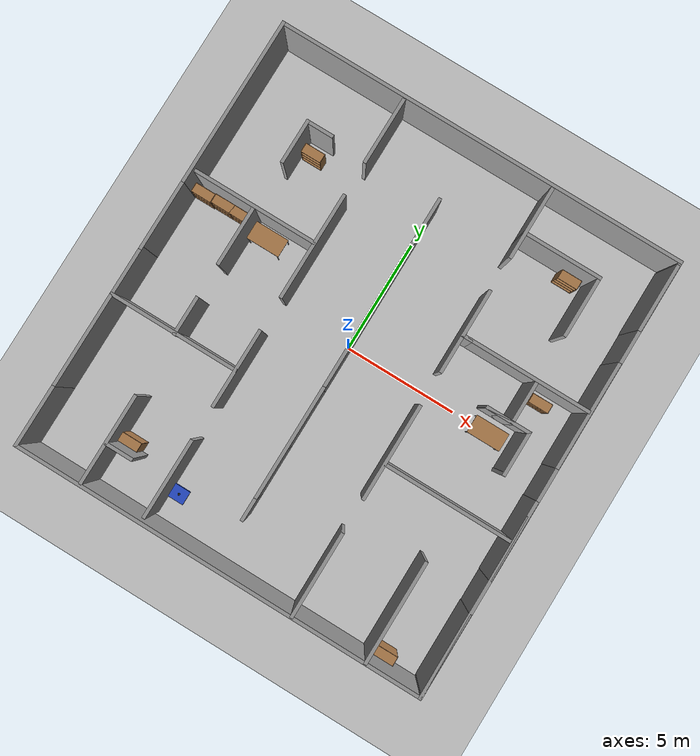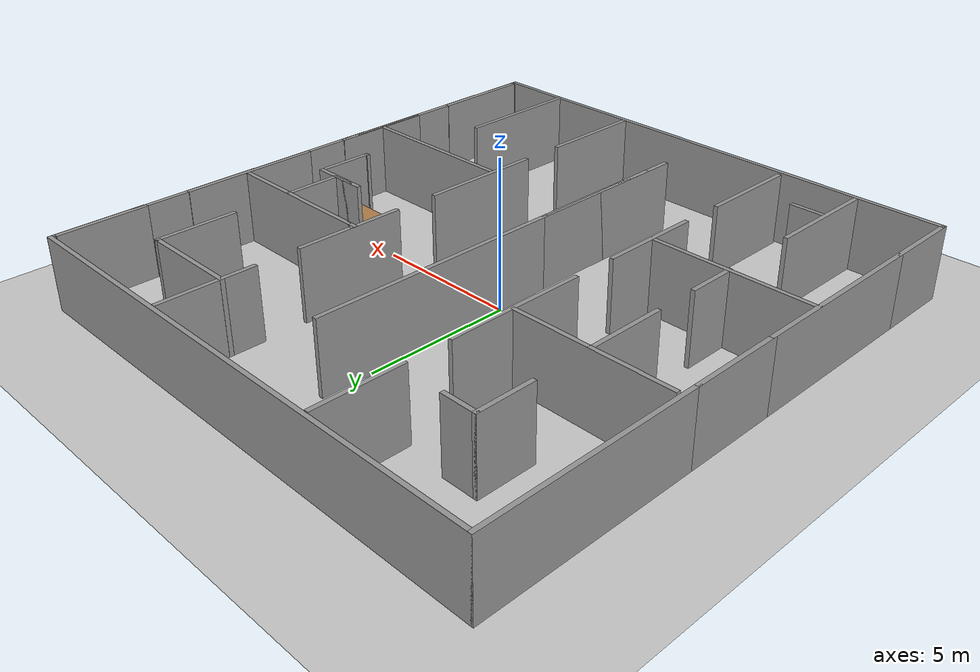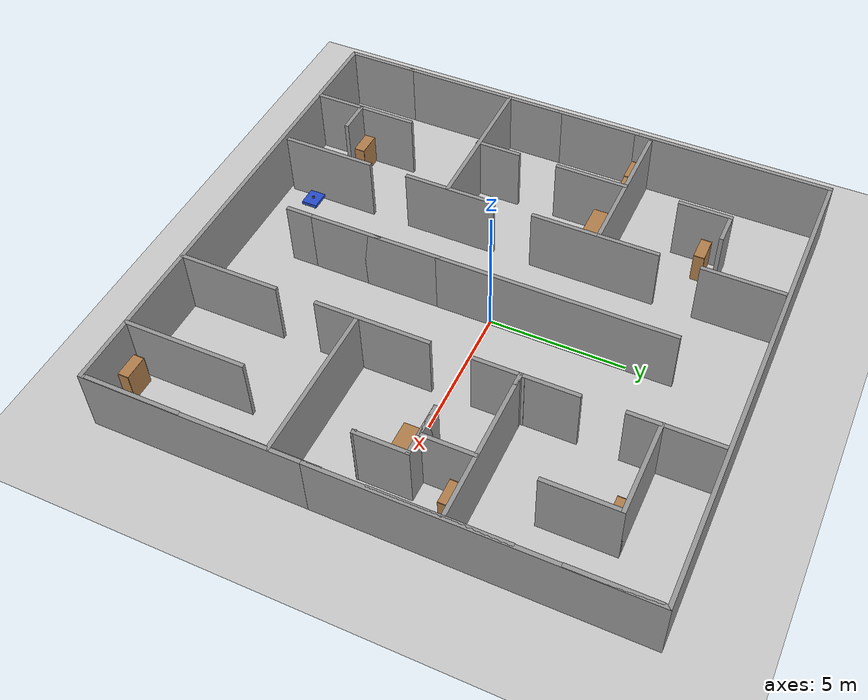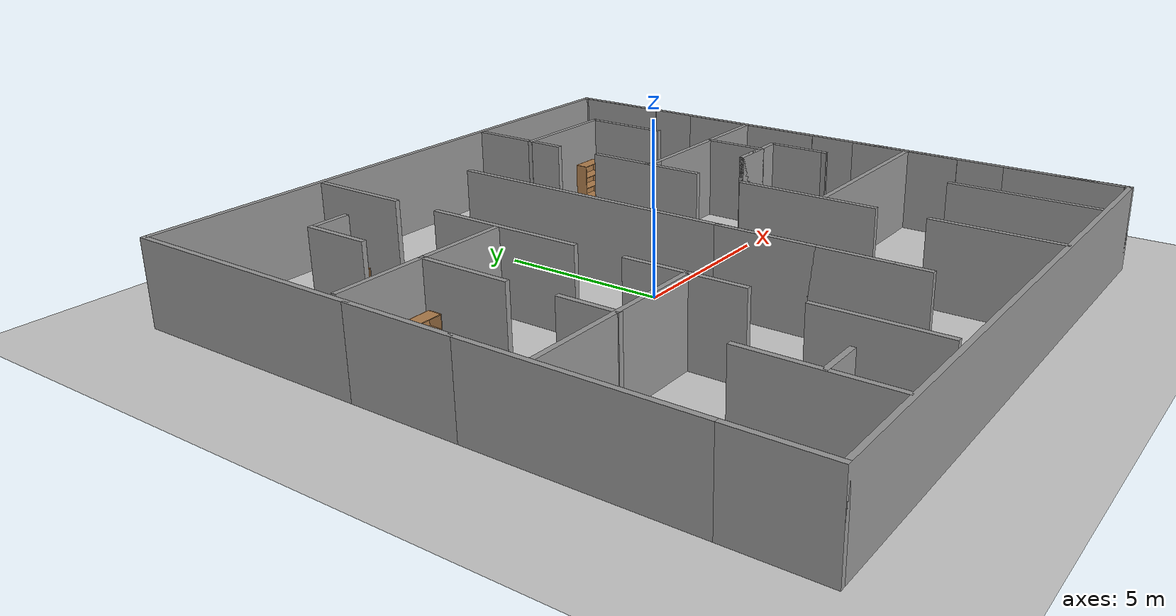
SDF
<sdf version="1.7">
 <world name="default">
  <light name="sun" type="directional">
   <pose>0 0 10 0 -0 0</pose>
   <diffuse>0.8 0.8 0.8 1</diffuse>
   <specular>0.2 0.2 0.2 1</specular>
   <attenuation>
    <range>1000</range>
    <constant>0.9</constant>
    <linear>0.01</linear>
    <quadratic>0.001</quadratic>
   </attenuation>
   <direction>-0.5 0.1 -0.9</direction>
   <spot><inner_angle>0</inner_angle><outer_angle>0</outer_angle><falloff>0</falloff></spot>
  </light>
  <model name="ground_plane">
   <static>1</static>
   <link name="link">
    <collision name="collision">
     <geometry><plane><normal>0 0 1</normal><size>100 100</size></plane></geometry>
     <surface>
      <contact><collide_bitmask>65535</collide_bitmask></contact>
      <friction><ode><mu>100</mu><mu2>50</mu2></ode></friction>
     </surface>
    </collision>
    <visual name="visual">
     <cast_shadows>0</cast_shadows>
     <geometry><plane><normal>0 0 1</normal><size>100 100</size></plane></geometry>
     <material>
      <script><uri>file://media/materials/scripts/gazebo.material</uri><name>Gazebo/Grey</name></script>
     </material>
    </visual>
   </link>
  </model>
  <gravity>0 0 -9.8</gravity>
  <magnetic_field>6e-06 2.3e-05 -4.2e-05</magnetic_field>
  <atmosphere type="adiabatic"/>
  <physics type="ode">
   <max_step_size>0.001</max_step_size>
   <real_time_factor>1</real_time_factor>
   <real_time_update_rate>1000</real_time_update_rate>
  </physics>
  <scene><ambient>0.4 0.4 0.4 1</ambient><background>0.7 0.7 0.7 1</background><shadows>1</shadows></scene>
  <audio><device>default</device></audio>
  <spherical_coordinates>
   <surface_model>EARTH_WGS84</surface_model>
   <latitude_deg>0</latitude_deg>
   <longitude_deg>0</longitude_deg>
   <elevation>0</elevation>
   <heading_deg>0</heading_deg>
  </spherical_coordinates>
  <model name="my_bot">
   <link name="base_link">
    <inertial>
     <pose>0 0 0.0345 0 -0 0</pose>
     <mass>1</mass>
     <inertia>
      <ixx>0.0393076</ixx>
      <ixy>0</ixy>
      <ixz>2.60209e-18</ixz>
      <iyy>0.0647243</iyy>
      <iyz>0</iyz>
      <izz>0.0875577</izz>
     </inertia>
    </inertial>
    <collision name="base_link_fixed_joint_lump__chassis_collision">
     <pose>0 0 0.083 0 -0 0</pose>
     <geometry><box><size>0.7 0.6 0.126</size></box></geometry>
    </collision>
    <collision name="base_link_fixed_joint_lump__caster1_wheel_collision_1">
     <pose>-0.3 0.2 -0.065 0 -0 0</pose>
     <geometry><sphere><radius>0.01</radius></sphere></geometry>
     <surface><friction><ode><mu>0.001</mu><mu2>0.001</mu2></ode></friction></surface>
    </collision>
    <collision name="base_link_fixed_joint_lump__caster2_wheel_collision_2">
     <pose>-0.3 -0.2 -0.065 0 -0 0</pose>
     <geometry><sphere><radius>0.01</radius></sphere></geometry>
     <surface><friction><ode><mu>0.001</mu><mu2>0.001</mu2></ode></friction></surface>
    </collision>
    <collision name="base_link_fixed_joint_lump__caster3_wheel_collision_3">
     <pose>0.3 -0.2 -0.065 0 -0 0</pose>
     <geometry><sphere><radius>0.01</radius></sphere></geometry>
     <surface><friction><ode><mu>0.001</mu><mu2>0.001</mu2></ode></friction></surface>
    </collision>
    <collision name="base_link_fixed_joint_lump__caster4_wheel_collision_4">
     <pose>0.3 0.2 -0.065 0 -0 0</pose>
     <geometry><sphere><radius>0.01</radius></sphere></geometry>
     <surface><friction><ode><mu>0.001</mu><mu2>0.001</mu2></ode></friction></surface>
    </collision>
    <collision name="base_link_fixed_joint_lump__laser_frame_collision_5">
     <pose>0 0 0.19 0 -0 0</pose>
     <geometry><cylinder><length>0.04</length><radius>0.05</radius></cylinder></geometry>
    </collision>
    <visual name="base_link_fixed_joint_lump__chassis_visual">
     <pose>0 0 0.083 0 -0 0</pose>
     <geometry><box><size>0.7 0.6 0.126</size></box></geometry>
     <material>
      <script><name>Gazebo/Blue</name><uri>file://media/materials/scripts/gazebo.material</uri></script>
     </material>
    </visual>
    <visual name="base_link_fixed_joint_lump__caster1_wheel_visual_1">
     <pose>-0.3 0.2 -0.065 0 -0 0</pose>
     <geometry><sphere><radius>0.01</radius></sphere></geometry>
     <material>
      <script><name>Gazebo/Blue</name><uri>file://media/materials/scripts/gazebo.material</uri></script>
     </material>
    </visual>
    <visual name="base_link_fixed_joint_lump__caster2_wheel_visual_2">
     <pose>-0.3 -0.2 -0.065 0 -0 0</pose>
     <geometry><sphere><radius>0.01</radius></sphere></geometry>
     <material>
      <script><name>Gazebo/Blue</name><uri>file://media/materials/scripts/gazebo.material</uri></script>
     </material>
    </visual>
    <visual name="base_link_fixed_joint_lump__caster3_wheel_visual_3">
     <pose>0.3 -0.2 -0.065 0 -0 0</pose>
     <geometry><sphere><radius>0.01</radius></sphere></geometry>
     <material>
      <script><name>Gazebo/Blue</name><uri>file://media/materials/scripts/gazebo.material</uri></script>
     </material>
    </visual>
    <visual name="base_link_fixed_joint_lump__caster4_wheel_visual_4">
     <pose>0.3 0.2 -0.065 0 -0 0</pose>
     <geometry><sphere><radius>0.01</radius></sphere></geometry>
     <material>
      <script><name>Gazebo/Blue</name><uri>file://media/materials/scripts/gazebo.material</uri></script>
     </material>
    </visual>
    <visual name="base_link_fixed_joint_lump__face_link_visual_5">
     <pose>0.35 0.05 0.093 3.14159 1.57079 3.14159</pose>
     <geometry><cylinder><length>0.002</length><radius>0.01</radius></cylinder></geometry>
     <material>
      <script><name>Gazebo/Black</name><uri>file://media/materials/scripts/gazebo.material</uri></script>
     </material>
    </visual>
    <visual name="base_link_fixed_joint_lump__face_link_visual_6">
     <pose>0.35 -0.05 0.093 3.14159 1.57079 3.14159</pose>
     <geometry><cylinder><length>0.002</length><radius>0.01</radius></cylinder></geometry>
     <material>
      <script><name>Gazebo/Black</name><uri>file://media/materials/scripts/gazebo.material</uri></script>
     </material>
    </visual>
    <visual name="base_link_fixed_joint_lump__face_link_visual_7">
     <pose>0.339 0 0.083 0 1.5 0</pose>
     <geometry><cylinder><length>0.02</length><radius>0.03</radius></cylinder></geometry>
     <material>
      <script><name>Gazebo/Black</name><uri>file://media/materials/scripts/gazebo.material</uri></script>
     </material>
    </visual>
    <visual name="base_link_fixed_joint_lump__laser_frame_visual_8">
     <pose>0 0 0.19 0 -0 0</pose>
     <geometry><cylinder><length>0.04</length><radius>0.05</radius></cylinder></geometry>
     <material>
      <script><name>Gazebo/Black</name><uri>file://media/materials/scripts/gazebo.material</uri></script>
     </material>
    </visual>
    <visual name="base_link_fixed_joint_lump__laser_frame_visual_9">
     <pose>0 0 0.14 0 -0 0</pose>
     <geometry><cylinder><length>0.1</length><radius>0.01</radius></cylinder></geometry>
     <material>
      <script><name>Gazebo/Black</name><uri>file://media/materials/scripts/gazebo.material</uri></script>
     </material>
    </visual>
    <sensor name="laser" type="ray">
     <visualize>1</visualize>
     <always_on>1</always_on>
     <update_rate>10</update_rate>
     <ray>
      <scan>
       <horizontal>
        <samples>360</samples>
        <resolution>1</resolution>
        <min_angle>-3.14</min_angle>
        <max_angle>3.14</max_angle>
       </horizontal>
       <vertical><samples>1</samples><min_angle>0</min_angle><max_angle>0</max_angle></vertical>
      </scan>
      <range><min>0.3</min><max>12</max><resolution>0.015</resolution></range>
      <noise><type>gaussian</type><mean>0</mean><stddev>0.01</stddev></noise>
     </ray>
     <plugin name="laser_controller" filename="libgazebo_ros_ray_sensor.so">
      <ros><remapping>~/out:=scan</remapping></ros>
      <output_type>sensor_msgs/LaserScan</output_type>
      <alwaysOn>1</alwaysOn>
      <updateRate>10</updateRate>
      <topicName>scan</topicName>
      <frame_name>laser_frame</frame_name>
      <output_type>sensor_msgs/LaserScan</output_type>
     </plugin>
     <pose>0 0 0.19 0 -0 0</pose>
    </sensor>
   </link>
   <joint name="left_wheel_joint" type="revolute">
    <pose relative_to="base_link">0 0.205 0 -1.5708 0 0</pose>
    <parent>base_link</parent>
    <child>left_wheel</child>
    <axis>
     <xyz>0 0 1</xyz>
     <limit><lower>-1e+16</lower><upper>1e+16</upper></limit>
     <dynamics><spring_reference>0</spring_reference><spring_stiffness>0</spring_stiffness></dynamics>
    </axis>
   </joint>
   <link name="left_wheel">
    <pose relative_to="left_wheel_joint">0 0 0 0 -0 0</pose>
    <inertial>
     <mass>0.05</mass>
     <inertia>
      <ixx>7.69792e-05</ixx>
      <ixy>0</ixy>
      <ixz>0</ixz>
      <iyy>7.69792e-05</iyy>
      <iyz>0</iyz>
      <izz>0.000140625</izz>
     </inertia>
    </inertial>
    <collision name="left_wheel_collision">
     <geometry><sphere><radius>0.075</radius></sphere></geometry>
    </collision>
    <visual name="left_wheel_visual">
     <geometry><cylinder><length>0.04</length><radius>0.075</radius></cylinder></geometry>
     <material>
      <script><name>Gazebo/Black</name><uri>file://media/materials/scripts/gazebo.material</uri></script>
     </material>
    </visual>
   </link>
   <joint name="right_wheel_joint" type="revolute">
    <pose relative_to="base_link">0 -0.205 0 1.5708 -0 0</pose>
    <parent>base_link</parent>
    <child>right_wheel</child>
    <axis>
     <xyz>0 0 -1</xyz>
     <limit><lower>-1e+16</lower><upper>1e+16</upper></limit>
     <dynamics><spring_reference>0</spring_reference><spring_stiffness>0</spring_stiffness></dynamics>
    </axis>
   </joint>
   <link name="right_wheel">
    <pose relative_to="right_wheel_joint">0 0 0 0 -0 0</pose>
    <inertial>
     <mass>0.05</mass>
     <inertia>
      <ixx>7.69792e-05</ixx>
      <ixy>0</ixy>
      <ixz>0</ixz>
      <iyy>7.69792e-05</iyy>
      <iyz>0</iyz>
      <izz>0.000140625</izz>
     </inertia>
    </inertial>
    <collision name="right_wheel_collision">
     <geometry><sphere><radius>0.075</radius></sphere></geometry>
    </collision>
    <visual name="right_wheel_visual">
     <geometry><cylinder><length>0.04</length><radius>0.075</radius></cylinder></geometry>
     <material>
      <script><name>Gazebo/Black</name><uri>file://media/materials/scripts/gazebo.material</uri></script>
     </material>
    </visual>
   </link>
   <static>0</static>
   <plugin name="gazebo_ros2_control" filename="libgazebo_ros2_control.so">
    <parameters>/home/robot/robot/install/ramabot/share/ramabot/config/my_controllers.yaml</parameters>
    <parameters>/home/robot/robot/install/ramabot/share/ramabot/config/gaz_ros2_ctl_use_sim.yaml</parameters>
   </plugin>
   <pose>-2.75861 -8.67534 0.074995 -2.5e-05 -0 -0.001635</pose>
  </model>
  <model name="tembok">
   <pose>0.235969 -0.259973 0 0 -0 0</pose>
   <link name="Wall_0">
    <collision name="Wall_0_Collision">
     <geometry><box><size>6.5 0.15 2.5</size></box></geometry>
     <pose>0 0 1.25 0 -0 0</pose>
    </collision>
    <visual name="Wall_0_Visual">
     <pose>0 0 1.25 0 -0 0</pose>
     <geometry><box><size>6.5 0.15 2.5</size></box></geometry>
     <material>
      <script><uri>file://media/materials/scripts/gazebo.material</uri><name>Gazebo/Grey</name></script>
      <ambient>1 1 1 1</ambient>
     </material>
     <meta><layer>0</layer></meta>
    </visual>
    <pose>-9.05 -3.925 0 0 -0 -1.5708</pose>
   </link>
   <link name="Wall_10">
    <collision name="Wall_10_Collision">
     <geometry><box><size>8 0.15 2.5</size></box></geometry>
     <pose>0 0 1.25 0 -0 0</pose>
    </collision>
    <visual name="Wall_10_Visual">
     <pose>0 0 1.25 0 -0 0</pose>
     <geometry><box><size>8 0.15 2.5</size></box></geometry>
     <material>
      <script><uri>file://media/materials/scripts/gazebo.material</uri><name>Gazebo/Grey</name></script>
      <ambient>1 1 1 1</ambient>
     </material>
     <meta><layer>0</layer></meta>
    </visual>
    <pose>9.05 -5.775 0 0 -0 1.5708</pose>
   </link>
   <link name="Wall_2">
    <collision name="Wall_2_Collision">
     <geometry><box><size>3.25 0.15 2.5</size></box></geometry>
     <pose>0 0 1.25 0 -0 0</pose>
    </collision>
    <visual name="Wall_2_Visual">
     <pose>0 0 1.25 0 -0 0</pose>
     <geometry><box><size>3.25 0.15 2.5</size></box></geometry>
     <material>
      <script><uri>file://media/materials/scripts/gazebo.material</uri><name>Gazebo/Grey</name></script>
      <ambient>1 1 1 1</ambient>
     </material>
     <meta><layer>0</layer></meta>
    </visual>
    <pose>-9.05 0.8 0 0 -0 1.5708</pose>
   </link>
   <link name="Wall_4">
    <collision name="Wall_4_Collision">
     <geometry><box><size>7.5 0.15 2.5</size></box></geometry>
     <pose>0 0 1.25 0 -0 0</pose>
    </collision>
    <visual name="Wall_4_Visual">
     <pose>0 0 1.25 0 -0 0</pose>
     <geometry><box><size>7.5 0.15 2.5</size></box></geometry>
     <material>
      <script><uri>file://media/materials/scripts/gazebo.material</uri><name>Gazebo/Grey</name></script>
      <ambient>1 1 1 1</ambient>
     </material>
     <meta><layer>0</layer></meta>
    </visual>
    <pose>-9.05 6.025 0 0 -0 1.5708</pose>
   </link>
   <link name="Wall_5">
    <collision name="Wall_5_Collision">
     <geometry><box><size>18.25 0.15 2.5</size></box></geometry>
     <pose>0 0 1.25 0 -0 0</pose>
    </collision>
    <visual name="Wall_5_Visual">
     <pose>0 0 1.25 0 -0 0</pose>
     <geometry><box><size>18.25 0.15 2.5</size></box></geometry>
     <material>
      <script><uri>file://media/materials/scripts/gazebo.material</uri><name>Gazebo/Grey</name></script>
      <ambient>1 1 1 1</ambient>
     </material>
     <meta><layer>0</layer></meta>
    </visual>
    <pose>-0 9.7 0 0 -0 0</pose>
   </link>
   <link name="Wall_6">
    <collision name="Wall_6_Collision">
     <geometry><box><size>12 0.15 2.5</size></box></geometry>
     <pose>0 0 1.25 0 -0 0</pose>
    </collision>
    <visual name="Wall_6_Visual">
     <pose>0 0 1.25 0 -0 0</pose>
     <geometry><box><size>12 0.15 2.5</size></box></geometry>
     <material>
      <script><uri>file://media/materials/scripts/gazebo.material</uri><name>Gazebo/Grey</name></script>
      <ambient>1 1 1 1</ambient>
     </material>
     <meta><layer>0</layer></meta>
    </visual>
    <pose>9.05 3.775 0 0 -0 -1.5708</pose>
   </link>
   <link name="Wall_8">
    <collision name="Wall_8_Collision">
     <geometry><box><size>2.75 0.15 2.5</size></box></geometry>
     <pose>0 0 1.25 0 -0 0</pose>
    </collision>
    <visual name="Wall_8_Visual">
     <pose>0 0 1.25 0 -0 0</pose>
     <geometry><box><size>2.75 0.15 2.5</size></box></geometry>
     <material>
      <script><uri>file://media/materials/scripts/gazebo.material</uri><name>Gazebo/Grey</name></script>
      <ambient>1 1 1 1</ambient>
     </material>
     <meta><layer>0</layer></meta>
    </visual>
    <pose>-9.05 -8.4 0 0 -0 -1.5708</pose>
   </link>
   <link name="Wall_9">
    <collision name="Wall_9_Collision">
     <geometry><box><size>18.25 0.15 2.5</size></box></geometry>
     <pose>0 0 1.25 0 -0 0</pose>
    </collision>
    <visual name="Wall_9_Visual">
     <pose>0 0 1.25 0 -0 0</pose>
     <geometry><box><size>18.25 0.15 2.5</size></box></geometry>
     <material>
      <script><uri>file://media/materials/scripts/gazebo.material</uri><name>Gazebo/Grey</name></script>
      <ambient>1 1 1 1</ambient>
     </material>
     <meta><layer>0</layer></meta>
    </visual>
    <pose>-0 -9.7 0 0 -0 0</pose>
   </link>
   <static>1</static>
  </model>
  <model name="samping">
   <pose>-3.71493 -0.202752 0 0 -0 0</pose>
   <link name="Wall_31">
    <collision name="Wall_31_Collision">
     <geometry><box><size>3 0.15 2.5</size></box></geometry>
     <pose>0 0 1.25 0 -0 0</pose>
    </collision>
    <visual name="Wall_31_Visual">
     <pose>0 0 1.25 0 -0 0</pose>
     <geometry><box><size>3 0.15 2.5</size></box></geometry>
     <material>
      <script><uri>file://media/materials/scripts/gazebo.material</uri><name>Gazebo/Grey</name></script>
      <ambient>1 1 1 1</ambient>
     </material>
     <meta><layer>0</layer></meta>
    </visual>
    <pose>0.530829 8.05 0 0 -0 -1.5708</pose>
   </link>
   <link name="Wall_33">
    <collision name="Wall_33_Collision">
     <geometry><box><size>4.75 0.15 2.5</size></box></geometry>
     <pose>0 0 1.25 0 -0 0</pose>
    </collision>
    <visual name="Wall_33_Visual">
     <pose>0 0 1.25 0 -0 0</pose>
     <geometry><box><size>4.75 0.15 2.5</size></box></geometry>
     <material>
      <script><uri>file://media/materials/scripts/gazebo.material</uri><name>Gazebo/Grey</name></script>
      <ambient>1 1 1 1</ambient>
     </material>
     <meta><layer>0</layer></meta>
    </visual>
    <pose>0.530829 2.725 0 0 -0 -1.5708</pose>
   </link>
   <link name="Wall_35">
    <collision name="Wall_35_Collision">
     <geometry><box><size>3.5 0.15 2.5</size></box></geometry>
     <pose>0 0 1.25 0 -0 0</pose>
    </collision>
    <visual name="Wall_35_Visual">
     <pose>0 0 1.25 0 -0 0</pose>
     <geometry><box><size>3.5 0.15 2.5</size></box></geometry>
     <material>
      <script><uri>file://media/materials/scripts/gazebo.material</uri><name>Gazebo/Grey</name></script>
      <ambient>1 1 1 1</ambient>
     </material>
     <meta><layer>0</layer></meta>
    </visual>
    <pose>0.530829 -2.85 0 0 -0 -1.5708</pose>
   </link>
   <link name="Wall_37">
    <collision name="Wall_37_Collision">
     <geometry><box><size>3.5 0.15 2.5</size></box></geometry>
     <pose>0 0 1.25 0 -0 0</pose>
    </collision>
    <visual name="Wall_37_Visual">
     <pose>0 0 1.25 0 -0 0</pose>
     <geometry><box><size>3.5 0.15 2.5</size></box></geometry>
     <material>
      <script><uri>file://media/materials/scripts/gazebo.material</uri><name>Gazebo/Grey</name></script>
      <ambient>1 1 1 1</ambient>
     </material>
     <meta><layer>0</layer></meta>
    </visual>
    <pose>0.530829 -7.8 0 0 -0 -1.5708</pose>
   </link>
   <link name="Wall_39">
    <collision name="Wall_39_Collision">
     <geometry><box><size>5.5 0.15 2.5</size></box></geometry>
     <pose>0 0 1.25 0 -0 0</pose>
    </collision>
    <visual name="Wall_39_Visual">
     <pose>0 0 1.25 0 -0 0</pose>
     <geometry><box><size>5.5 0.15 2.5</size></box></geometry>
     <material>
      <script><uri>file://media/materials/scripts/gazebo.material</uri><name>Gazebo/Grey</name></script>
      <ambient>1 1 1 1</ambient>
     </material>
     <meta><layer>0</layer></meta>
    </visual>
    <pose>-2.19664 2.86376 0 0 -0 3.14159</pose>
   </link>
   <link name="Wall_41">
    <collision name="Wall_41_Collision">
     <geometry><box><size>5.75 0.15 2.5</size></box></geometry>
     <pose>0 0 1.25 0 -0 0</pose>
    </collision>
    <visual name="Wall_41_Visual">
     <pose>0 0 1.25 0 -0 0</pose>
     <geometry><box><size>5.75 0.15 2.5</size></box></geometry>
     <material>
      <script><uri>file://media/materials/scripts/gazebo.material</uri><name>Gazebo/Grey</name></script>
      <ambient>1 1 1 1</ambient>
     </material>
     <meta><layer>0</layer></meta>
    </visual>
    <pose>-2.28666 -2.92545 0 0 -0 3.14159</pose>
   </link>
   <static>1</static>
  </model>
  <model name="samping_0">
   <pose>8.73859 -0.259974 0 0 -0 0</pose>
   <link name="Wall_31">
    <collision name="Wall_31_Collision">
     <geometry><box><size>3 0.15 2.5</size></box></geometry>
     <pose>0 0 1.25 0 -0 0</pose>
    </collision>
    <visual name="Wall_31_Visual">
     <pose>0 0 1.25 0 -0 0</pose>
     <geometry><box><size>3 0.15 2.5</size></box></geometry>
     <material>
      <script><uri>file://media/materials/scripts/gazebo.material</uri><name>Gazebo/Grey</name></script>
      <ambient>1 1 1 1</ambient>
     </material>
     <meta><layer>0</layer></meta>
    </visual>
    <pose>0.530829 8.05 0 0 -0 -1.5708</pose>
   </link>
   <link name="Wall_33">
    <collision name="Wall_33_Collision">
     <geometry><box><size>4.75 0.15 2.5</size></box></geometry>
     <pose>0 0 1.25 0 -0 0</pose>
    </collision>
    <visual name="Wall_33_Visual">
     <pose>0 0 1.25 0 -0 0</pose>
     <geometry><box><size>4.75 0.15 2.5</size></box></geometry>
     <material>
      <script><uri>file://media/materials/scripts/gazebo.material</uri><name>Gazebo/Grey</name></script>
      <ambient>1 1 1 1</ambient>
     </material>
     <meta><layer>0</layer></meta>
    </visual>
    <pose>0.530829 2.725 0 0 -0 -1.5708</pose>
   </link>
   <link name="Wall_35">
    <collision name="Wall_35_Collision">
     <geometry><box><size>3.5 0.15 2.5</size></box></geometry>
     <pose>0 0 1.25 0 -0 0</pose>
    </collision>
    <visual name="Wall_35_Visual">
     <pose>0 0 1.25 0 -0 0</pose>
     <geometry><box><size>3.5 0.15 2.5</size></box></geometry>
     <material>
      <script><uri>file://media/materials/scripts/gazebo.material</uri><name>Gazebo/Grey</name></script>
      <ambient>1 1 1 1</ambient>
     </material>
     <meta><layer>0</layer></meta>
    </visual>
    <pose>0.530829 -2.85 0 0 -0 -1.5708</pose>
   </link>
   <link name="Wall_37">
    <collision name="Wall_37_Collision">
     <geometry><box><size>3.5 0.15 2.5</size></box></geometry>
     <pose>0 0 1.25 0 -0 0</pose>
    </collision>
    <visual name="Wall_37_Visual">
     <pose>0 0 1.25 0 -0 0</pose>
     <geometry><box><size>3.5 0.15 2.5</size></box></geometry>
     <material>
      <script><uri>file://media/materials/scripts/gazebo.material</uri><name>Gazebo/Grey</name></script>
      <ambient>1 1 1 1</ambient>
     </material>
     <meta><layer>0</layer></meta>
    </visual>
    <pose>0.530829 -7.8 0 0 -0 -1.5708</pose>
   </link>
   <link name="Wall_39">
    <collision name="Wall_39_Collision">
     <geometry><box><size>5.5 0.15 2.5</size></box></geometry>
     <pose>0 0 1.25 0 -0 0</pose>
    </collision>
    <visual name="Wall_39_Visual">
     <pose>0 0 1.25 0 -0 0</pose>
     <geometry><box><size>5.5 0.15 2.5</size></box></geometry>
     <material>
      <script><uri>file://media/materials/scripts/gazebo.material</uri><name>Gazebo/Grey</name></script>
      <ambient>1 1 1 1</ambient>
     </material>
     <meta><layer>0</layer></meta>
    </visual>
    <pose>-2.19664 2.86376 0 0 -0 3.14159</pose>
   </link>
   <link name="Wall_41">
    <collision name="Wall_41_Collision">
     <geometry><box><size>5.75 0.15 2.5</size></box></geometry>
     <pose>0 0 1.25 0 -0 0</pose>
    </collision>
    <visual name="Wall_41_Visual">
     <pose>0 0 1.25 0 -0 0</pose>
     <geometry><box><size>5.75 0.15 2.5</size></box></geometry>
     <material>
      <script><uri>file://media/materials/scripts/gazebo.material</uri><name>Gazebo/Grey</name></script>
      <ambient>1 1 1 1</ambient>
     </material>
     <meta><layer>0</layer></meta>
    </visual>
    <pose>-2.28666 -2.92545 0 0 -0 3.14159</pose>
   </link>
   <static>1</static>
  </model>
  <model name="samping3">
   <pose>0.878279 -0.32056 0 0 -0 0</pose>
   <link name="Wall_11">
    <collision name="Wall_11_Collision">
     <geometry><box><size>3.25 0.15 2.5</size></box></geometry>
     <pose>0 0 1.25 0 -0 0</pose>
    </collision>
    <visual name="Wall_11_Visual">
     <pose>0 0 1.25 0 -0 0</pose>
     <geometry><box><size>3.25 0.15 2.5</size></box></geometry>
     <material>
      <script><uri>file://media/materials/scripts/gazebo.material</uri><name>Gazebo/Grey</name></script>
      <ambient>1 1 1 1</ambient>
     </material>
     <meta><layer>0</layer></meta>
    </visual>
    <pose>2.69955 8.05362 0 0 -0 1.5708</pose>
   </link>
   <link name="Wall_2">
    <collision name="Wall_2_Collision">
     <geometry><box><size>4.25 0.15 2.5</size></box></geometry>
     <pose>0 0 1.25 0 -0 0</pose>
    </collision>
    <visual name="Wall_2_Visual">
     <pose>0 0 1.25 0 -0 0</pose>
     <geometry><box><size>4.25 0.15 2.5</size></box></geometry>
     <material>
      <script><uri>file://media/materials/scripts/gazebo.material</uri><name>Gazebo/Grey</name></script>
      <ambient>1 1 1 1</ambient>
     </material>
     <meta><layer>0</layer></meta>
    </visual>
    <pose>2.69955 -2.34638 0 0 -0 -1.5708</pose>
   </link>
   <link name="Wall_21">
    <collision name="Wall_21_Collision">
     <geometry><box><size>0.25 0.15 2.5</size></box></geometry>
     <pose>0 0 1.25 0 -0 0</pose>
    </collision>
    <visual name="Wall_21_Visual">
     <pose>0 0 1.25 0 -0 0</pose>
     <geometry><box><size>0.25 0.15 2.5</size></box></geometry>
     <material>
      <script><uri>file://media/materials/scripts/gazebo.material</uri><name>Gazebo/Grey</name></script>
      <ambient>1 1 1 1</ambient>
     </material>
     <meta><layer>0</layer></meta>
    </visual>
    <pose>2.70984 2.97166 0 0 -0 -1.5708</pose>
   </link>
   <link name="Wall_22">
    <collision name="Wall_22_Collision">
     <geometry><box><size>0.5 0.15 2.5</size></box></geometry>
     <pose>0 0 1.25 0 -0 0</pose>
    </collision>
    <visual name="Wall_22_Visual">
     <pose>0 0 1.25 0 -0 0</pose>
     <geometry><box><size>0.5 0.15 2.5</size></box></geometry>
     <material>
      <script><uri>file://media/materials/scripts/gazebo.material</uri><name>Gazebo/Grey</name></script>
      <ambient>1 1 1 1</ambient>
     </material>
     <meta><layer>0</layer></meta>
    </visual>
    <pose>2.88484 2.92166 0 0 -0 0</pose>
   </link>
   <link name="Wall_24">
    <collision name="Wall_24_Collision">
     <geometry><box><size>3.5 0.15 2.5</size></box></geometry>
     <pose>0 0 1.25 0 -0 0</pose>
    </collision>
    <visual name="Wall_24_Visual">
     <pose>0 0 1.25 0 -0 0</pose>
     <geometry><box><size>3.5 0.15 2.5</size></box></geometry>
     <material>
      <script><uri>file://media/materials/scripts/gazebo.material</uri><name>Gazebo/Grey</name></script>
      <ambient>1 1 1 1</ambient>
     </material>
     <meta><layer>0</layer></meta>
    </visual>
    <pose>4.37148 7.58996 0 0 -0 0</pose>
   </link>
   <link name="Wall_25">
    <collision name="Wall_25_Collision">
     <geometry><box><size>2.75 0.15 2.5</size></box></geometry>
     <pose>0 0 1.25 0 -0 0</pose>
    </collision>
    <visual name="Wall_25_Visual">
     <pose>0 0 1.25 0 -0 0</pose>
     <geometry><box><size>2.75 0.15 2.5</size></box></geometry>
     <material>
      <script><uri>file://media/materials/scripts/gazebo.material</uri><name>Gazebo/Grey</name></script>
      <ambient>1 1 1 1</ambient>
     </material>
     <meta><layer>0</layer></meta>
    </visual>
    <pose>6.04648 6.28996 0 0 -0 -1.5708</pose>
   </link>
   <link name="Wall_28">
    <collision name="Wall_28_Collision">
     <geometry><box><size>2 0.15 2.5</size></box></geometry>
     <pose>0 0 1.25 0 -0 0</pose>
    </collision>
    <visual name="Wall_28_Visual">
     <pose>0 0 1.25 0 -0 0</pose>
     <geometry><box><size>2 0.15 2.5</size></box></geometry>
     <material>
      <script><uri>file://media/materials/scripts/gazebo.material</uri><name>Gazebo/Grey</name></script>
      <ambient>1 1 1 1</ambient>
     </material>
     <meta><layer>0</layer></meta>
    </visual>
    <pose>6.04648 1.96496 0 0 -0 -1.5708</pose>
   </link>
   <link name="Wall_29">
    <collision name="Wall_29_Collision">
     <geometry><box><size>1.25 0.15 2.5</size></box></geometry>
     <pose>0 0 1.25 0 -0 0</pose>
    </collision>
    <visual name="Wall_29_Visual">
     <pose>0 0 1.25 0 -0 0</pose>
     <geometry><box><size>1.25 0.15 2.5</size></box></geometry>
     <material>
      <script><uri>file://media/materials/scripts/gazebo.material</uri><name>Gazebo/Grey</name></script>
      <ambient>1 1 1 1</ambient>
     </material>
     <meta><layer>0</layer></meta>
    </visual>
    <pose>5.49648 1.03996 0 0 -0 3.14159</pose>
   </link>
   <link name="Wall_30">
    <collision name="Wall_30_Collision">
     <geometry><box><size>2 0.15 2.5</size></box></geometry>
     <pose>0 0 1.25 0 -0 0</pose>
    </collision>
    <visual name="Wall_30_Visual">
     <pose>0 0 1.25 0 -0 0</pose>
     <geometry><box><size>2 0.15 2.5</size></box></geometry>
     <material>
      <script><uri>file://media/materials/scripts/gazebo.material</uri><name>Gazebo/Grey</name></script>
      <ambient>1 1 1 1</ambient>
     </material>
     <meta><layer>0</layer></meta>
    </visual>
    <pose>5.87148 1.03996 0 0 -0 0</pose>
   </link>
   <link name="Wall_31">
    <collision name="Wall_31_Collision">
     <geometry><box><size>2 0.15 2.5</size></box></geometry>
     <pose>0 0 1.25 0 -0 0</pose>
    </collision>
    <visual name="Wall_31_Visual">
     <pose>0 0 1.25 0 -0 0</pose>
     <geometry><box><size>2 0.15 2.5</size></box></geometry>
     <material>
      <script><uri>file://media/materials/scripts/gazebo.material</uri><name>Gazebo/Grey</name></script>
      <ambient>1 1 1 1</ambient>
     </material>
     <meta><layer>0</layer></meta>
    </visual>
    <pose>6.79648 0.114957 0 0 -0 -1.5708</pose>
   </link>
   <link name="Wall_33">
    <collision name="Wall_33_Collision">
     <geometry><box><size>0.169397 0.15 2.5</size></box></geometry>
     <pose>0 0 1.25 0 -0 0</pose>
    </collision>
    <visual name="Wall_33_Visual">
     <pose>0 0 1.25 0 -0 0</pose>
     <geometry><box><size>0.169397 0.15 2.5</size></box></geometry>
     <material>
      <script><uri>file://media/materials/scripts/gazebo.material</uri><name>Gazebo/Grey</name></script>
      <ambient>1 1 1 1</ambient>
     </material>
     <meta><layer>0</layer></meta>
    </visual>
    <pose>6.78699 -0.812016 0 0 -0 -2.93676</pose>
   </link>
   <link name="Wall_36">
    <collision name="Wall_36_Collision">
     <geometry><box><size>4.5 0.15 2.5</size></box></geometry>
     <pose>0 0 1.25 0 -0 0</pose>
    </collision>
    <visual name="Wall_36_Visual">
     <pose>0 0 1.25 0 -0 0</pose>
     <geometry><box><size>4.5 0.15 2.5</size></box></geometry>
     <material>
      <script><uri>file://media/materials/scripts/gazebo.material</uri><name>Gazebo/Grey</name></script>
      <ambient>1 1 1 1</ambient>
     </material>
     <meta><layer>0</layer></meta>
    </visual>
    <pose>5.98105 -7.42862 0 0 -0 1.5708</pose>
   </link>
   <link name="Wall_4">
    <collision name="Wall_4_Collision">
     <geometry><box><size>3.75 0.15 2.5</size></box></geometry>
     <pose>0 0 1.25 0 -0 0</pose>
    </collision>
    <visual name="Wall_4_Visual">
     <pose>0 0 1.25 0 -0 0</pose>
     <geometry><box><size>3.75 0.15 2.5</size></box></geometry>
     <material>
      <script><uri>file://media/materials/scripts/gazebo.material</uri><name>Gazebo/Grey</name></script>
      <ambient>1 1 1 1</ambient>
     </material>
     <meta><layer>0</layer></meta>
    </visual>
    <pose>2.69955 -7.79638 0 0 -0 -1.5708</pose>
   </link>
   <link name="Wall_40">
    <collision name="Wall_40_Collision">
     <geometry><box><size>4 0.15 2.5</size></box></geometry>
     <pose>0 0 1.25 0 -0 0</pose>
    </collision>
    <visual name="Wall_40_Visual">
     <pose>0 0 1.25 0 -0 0</pose>
     <geometry><box><size>4 0.15 2.5</size></box></geometry>
     <material>
      <script><uri>file://media/materials/scripts/gazebo.material</uri><name>Gazebo/Grey</name></script>
      <ambient>1 1 1 1</ambient>
     </material>
     <meta><layer>0</layer></meta>
    </visual>
    <pose>-6.81017 -7.60923 0 0 -0 1.5708</pose>
   </link>
   <link name="Wall_45">
    <collision name="Wall_45_Collision">
     <geometry><box><size>2.75 0.15 2.5</size></box></geometry>
     <pose>0 0 1.25 0 -0 0</pose>
    </collision>
    <visual name="Wall_45_Visual">
     <pose>0 0 1.25 0 -0 0</pose>
     <geometry><box><size>2.75 0.15 2.5</size></box></geometry>
     <material>
      <script><uri>file://media/materials/scripts/gazebo.material</uri><name>Gazebo/Grey</name></script>
      <ambient>1 1 1 1</ambient>
     </material>
     <meta><layer>0</layer></meta>
    </visual>
    <pose>-6.81017 1.66577 0 0 -0 1.5708</pose>
   </link>
   <link name="Wall_47">
    <collision name="Wall_47_Collision">
     <geometry><box><size>2 0.15 2.5</size></box></geometry>
     <pose>0 0 1.25 0 -0 0</pose>
    </collision>
    <visual name="Wall_47_Visual">
     <pose>0 0 1.25 0 -0 0</pose>
     <geometry><box><size>2 0.15 2.5</size></box></geometry>
     <material>
      <script><uri>file://media/materials/scripts/gazebo.material</uri><name>Gazebo/Grey</name></script>
      <ambient>1 1 1 1</ambient>
     </material>
     <meta><layer>0</layer></meta>
    </visual>
    <pose>-6.81017 5.99077 0 0 -0 1.5708</pose>
   </link>
   <link name="Wall_48">
    <collision name="Wall_48_Collision">
     <geometry><box><size>1.25 0.15 2.5</size></box></geometry>
     <pose>0 0 1.25 0 -0 0</pose>
    </collision>
    <visual name="Wall_48_Visual">
     <pose>0 0 1.25 0 -0 0</pose>
     <geometry><box><size>1.25 0.15 2.5</size></box></geometry>
     <material>
      <script><uri>file://media/materials/scripts/gazebo.material</uri><name>Gazebo/Grey</name></script>
      <ambient>1 1 1 1</ambient>
     </material>
     <meta><layer>0</layer></meta>
    </visual>
    <pose>-6.26017 6.91577 0 0 -0 0</pose>
   </link>
   <link name="Wall_50">
    <collision name="Wall_50_Collision">
     <geometry><box><size>1.75 0.15 2.5</size></box></geometry>
     <pose>0 0 1.25 0 -0 0</pose>
    </collision>
    <visual name="Wall_50_Visual">
     <pose>0 0 1.25 0 -0 0</pose>
     <geometry><box><size>1.75 0.15 2.5</size></box></geometry>
     <material>
      <script><uri>file://media/materials/scripts/gazebo.material</uri><name>Gazebo/Grey</name></script>
      <ambient>1 1 1 1</ambient>
     </material>
     <meta><layer>0</layer></meta>
    </visual>
    <pose>-6.81017 -2.03423 0 0 -0 1.5708</pose>
   </link>
   <link name="Wall_52">
    <collision name="Wall_52_Collision">
     <geometry><box><size>1.25 0.15 2.5</size></box></geometry>
     <pose>0 0 1.25 0 -0 0</pose>
    </collision>
    <visual name="Wall_52_Visual">
     <pose>0 0 1.25 0 -0 0</pose>
     <geometry><box><size>1.25 0.15 2.5</size></box></geometry>
     <material>
      <script><uri>file://media/materials/scripts/gazebo.material</uri><name>Gazebo/Grey</name></script>
      <ambient>1 1 1 1</ambient>
     </material>
     <meta><layer>0</layer></meta>
    </visual>
    <pose>-6.21391 -7.7763 0 0 -0 0</pose>
   </link>
   <link name="Wall_7">
    <collision name="Wall_7_Collision">
     <geometry><box><size>3.75 0.15 2.5</size></box></geometry>
     <pose>0 0 1.25 0 -0 0</pose>
    </collision>
    <visual name="Wall_7_Visual">
     <pose>0 0 1.25 0 -0 0</pose>
     <geometry><box><size>3.75 0.15 2.5</size></box></geometry>
     <material>
      <script><uri>file://media/materials/scripts/gazebo.material</uri><name>Gazebo/Grey</name></script>
      <ambient>1 1 1 1</ambient>
     </material>
     <meta><layer>0</layer></meta>
    </visual>
    <pose>2.69955 3.10362 0 0 -0 1.5708</pose>
   </link>
   <static>1</static>
  </model>
  <model name="bookshelf">
   <static>1</static>
   <link name="link">
    <inertial><mass>1</mass></inertial>
    <collision name="back">
     <pose>0 0.005 0.6 0 -0 0</pose>
     <geometry><box><size>0.9 0.01 1.2</size></box></geometry>
    </collision>
    <visual name="visual1">
     <pose>0 0.005 0.6 0 -0 0</pose>
     <geometry><box><size>0.9 0.01 1.2</size></box></geometry>
     <material>
      <script><uri>file://media/materials/scripts/gazebo.material</uri><name>Gazebo/Wood</name></script>
     </material>
    </visual>
    <collision name="left_side">
     <pose>0.45 -0.195 0.6 0 -0 0</pose>
     <geometry><box><size>0.02 0.4 1.2</size></box></geometry>
    </collision>
    <visual name="visual2">
     <pose>0.45 -0.195 0.6 0 -0 0</pose>
     <geometry><box><size>0.02 0.4 1.2</size></box></geometry>
     <material>
      <script><uri>file://media/materials/scripts/gazebo.material</uri><name>Gazebo/Wood</name></script>
     </material>
    </visual>
    <collision name="right_side">
     <pose>-0.45 -0.195 0.6 0 -0 0</pose>
     <geometry><box><size>0.02 0.4 1.2</size></box></geometry>
    </collision>
    <visual name="visual3">
     <pose>-0.45 -0.195 0.6 0 -0 0</pose>
     <geometry><box><size>0.02 0.4 1.2</size></box></geometry>
     <material>
      <script><uri>file://media/materials/scripts/gazebo.material</uri><name>Gazebo/Wood</name></script>
     </material>
    </visual>
    <collision name="bottom">
     <pose>0 -0.195 0.03 0 -0 0</pose>
     <geometry><box><size>0.88 0.4 0.06</size></box></geometry>
    </collision>
    <visual name="visual4">
     <pose>0 -0.195 0.03 0 -0 0</pose>
     <geometry><box><size>0.88 0.4 0.06</size></box></geometry>
     <material>
      <script><uri>file://media/materials/scripts/gazebo.material</uri><name>Gazebo/Wood</name></script>
     </material>
    </visual>
    <collision name="top">
     <pose>0 -0.195 1.19 0 -0 0</pose>
     <geometry><box><size>0.88 0.4 0.02</size></box></geometry>
    </collision>
    <visual name="visual5">
     <pose>0 -0.195 1.19 0 -0 0</pose>
     <geometry><box><size>0.88 0.4 0.02</size></box></geometry>
     <material>
      <script><uri>file://media/materials/scripts/gazebo.material</uri><name>Gazebo/Wood</name></script>
     </material>
    </visual>
    <collision name="low_shelf">
     <pose>0 -0.195 0.43 0 -0 0</pose>
     <geometry><box><size>0.88 0.4 0.02</size></box></geometry>
    </collision>
    <visual name="visual6">
     <pose>0 -0.195 0.43 0 -0 0</pose>
     <geometry><box><size>0.88 0.4 0.02</size></box></geometry>
     <material>
      <script><uri>file://media/materials/scripts/gazebo.material</uri><name>Gazebo/Wood</name></script>
     </material>
    </visual>
    <collision name="high_shelf">
     <pose>0 -0.195 0.8 0 -0 0</pose>
     <geometry><box><size>0.88 0.4 0.02</size></box></geometry>
    </collision>
    <visual name="visual7">
     <pose>0 -0.195 0.8 0 -0 0</pose>
     <geometry><box><size>0.88 0.4 0.02</size></box></geometry>
     <material>
      <script><uri>file://media/materials/scripts/gazebo.material</uri><name>Gazebo/Wood</name></script>
     </material>
    </visual>
   </link>
   <pose>6.14593 7.12294 0 0 -0 0</pose>
  </model>
  <model name="bookshelf_0">
   <static>1</static>
   <link name="link">
    <inertial><mass>1</mass></inertial>
    <collision name="back">
     <pose>0 0.005 0.6 0 -0 0</pose>
     <geometry><box><size>0.9 0.01 1.2</size></box></geometry>
    </collision>
    <visual name="visual1">
     <pose>0 0.005 0.6 0 -0 0</pose>
     <geometry><box><size>0.9 0.01 1.2</size></box></geometry>
     <material>
      <script><uri>file://media/materials/scripts/gazebo.material</uri><name>Gazebo/Wood</name></script>
     </material>
    </visual>
    <collision name="left_side">
     <pose>0.45 -0.195 0.6 0 -0 0</pose>
     <geometry><box><size>0.02 0.4 1.2</size></box></geometry>
    </collision>
    <visual name="visual2">
     <pose>0.45 -0.195 0.6 0 -0 0</pose>
     <geometry><box><size>0.02 0.4 1.2</size></box></geometry>
     <material>
      <script><uri>file://media/materials/scripts/gazebo.material</uri><name>Gazebo/Wood</name></script>
     </material>
    </visual>
    <collision name="right_side">
     <pose>-0.45 -0.195 0.6 0 -0 0</pose>
     <geometry><box><size>0.02 0.4 1.2</size></box></geometry>
    </collision>
    <visual name="visual3">
     <pose>-0.45 -0.195 0.6 0 -0 0</pose>
     <geometry><box><size>0.02 0.4 1.2</size></box></geometry>
     <material>
      <script><uri>file://media/materials/scripts/gazebo.material</uri><name>Gazebo/Wood</name></script>
     </material>
    </visual>
    <collision name="bottom">
     <pose>0 -0.195 0.03 0 -0 0</pose>
     <geometry><box><size>0.88 0.4 0.06</size></box></geometry>
    </collision>
    <visual name="visual4">
     <pose>0 -0.195 0.03 0 -0 0</pose>
     <geometry><box><size>0.88 0.4 0.06</size></box></geometry>
     <material>
      <script><uri>file://media/materials/scripts/gazebo.material</uri><name>Gazebo/Wood</name></script>
     </material>
    </visual>
    <collision name="top">
     <pose>0 -0.195 1.19 0 -0 0</pose>
     <geometry><box><size>0.88 0.4 0.02</size></box></geometry>
    </collision>
    <visual name="visual5">
     <pose>0 -0.195 1.19 0 -0 0</pose>
     <geometry><box><size>0.88 0.4 0.02</size></box></geometry>
     <material>
      <script><uri>file://media/materials/scripts/gazebo.material</uri><name>Gazebo/Wood</name></script>
     </material>
    </visual>
    <collision name="low_shelf">
     <pose>0 -0.195 0.43 0 -0 0</pose>
     <geometry><box><size>0.88 0.4 0.02</size></box></geometry>
    </collision>
    <visual name="visual6">
     <pose>0 -0.195 0.43 0 -0 0</pose>
     <geometry><box><size>0.88 0.4 0.02</size></box></geometry>
     <material>
      <script><uri>file://media/materials/scripts/gazebo.material</uri><name>Gazebo/Wood</name></script>
     </material>
    </visual>
    <collision name="high_shelf">
     <pose>0 -0.195 0.8 0 -0 0</pose>
     <geometry><box><size>0.88 0.4 0.02</size></box></geometry>
    </collision>
    <visual name="visual7">
     <pose>0 -0.195 0.8 0 -0 0</pose>
     <geometry><box><size>0.88 0.4 0.02</size></box></geometry>
     <material>
      <script><uri>file://media/materials/scripts/gazebo.material</uri><name>Gazebo/Wood</name></script>
     </material>
    </visual>
   </link>
   <pose>-5.33418 6.12104 0 0 -0 0</pose>
  </model>
  <model name="bookshelf_1">
   <static>1</static>
   <link name="link">
    <inertial><mass>1</mass></inertial>
    <collision name="back">
     <pose>0 0.005 0.6 0 -0 0</pose>
     <geometry><box><size>0.9 0.01 1.2</size></box></geometry>
    </collision>
    <visual name="visual1">
     <pose>0 0.005 0.6 0 -0 0</pose>
     <geometry><box><size>0.9 0.01 1.2</size></box></geometry>
     <material>
      <script><uri>file://media/materials/scripts/gazebo.material</uri><name>Gazebo/Wood</name></script>
     </material>
    </visual>
    <collision name="left_side">
     <pose>0.45 -0.195 0.6 0 -0 0</pose>
     <geometry><box><size>0.02 0.4 1.2</size></box></geometry>
    </collision>
    <visual name="visual2">
     <pose>0.45 -0.195 0.6 0 -0 0</pose>
     <geometry><box><size>0.02 0.4 1.2</size></box></geometry>
     <material>
      <script><uri>file://media/materials/scripts/gazebo.material</uri><name>Gazebo/Wood</name></script>
     </material>
    </visual>
    <collision name="right_side">
     <pose>-0.45 -0.195 0.6 0 -0 0</pose>
     <geometry><box><size>0.02 0.4 1.2</size></box></geometry>
    </collision>
    <visual name="visual3">
     <pose>-0.45 -0.195 0.6 0 -0 0</pose>
     <geometry><box><size>0.02 0.4 1.2</size></box></geometry>
     <material>
      <script><uri>file://media/materials/scripts/gazebo.material</uri><name>Gazebo/Wood</name></script>
     </material>
    </visual>
    <collision name="bottom">
     <pose>0 -0.195 0.03 0 -0 0</pose>
     <geometry><box><size>0.88 0.4 0.06</size></box></geometry>
    </collision>
    <visual name="visual4">
     <pose>0 -0.195 0.03 0 -0 0</pose>
     <geometry><box><size>0.88 0.4 0.06</size></box></geometry>
     <material>
      <script><uri>file://media/materials/scripts/gazebo.material</uri><name>Gazebo/Wood</name></script>
     </material>
    </visual>
    <collision name="top">
     <pose>0 -0.195 1.19 0 -0 0</pose>
     <geometry><box><size>0.88 0.4 0.02</size></box></geometry>
    </collision>
    <visual name="visual5">
     <pose>0 -0.195 1.19 0 -0 0</pose>
     <geometry><box><size>0.88 0.4 0.02</size></box></geometry>
     <material>
      <script><uri>file://media/materials/scripts/gazebo.material</uri><name>Gazebo/Wood</name></script>
     </material>
    </visual>
    <collision name="low_shelf">
     <pose>0 -0.195 0.43 0 -0 0</pose>
     <geometry><box><size>0.88 0.4 0.02</size></box></geometry>
    </collision>
    <visual name="visual6">
     <pose>0 -0.195 0.43 0 -0 0</pose>
     <geometry><box><size>0.88 0.4 0.02</size></box></geometry>
     <material>
      <script><uri>file://media/materials/scripts/gazebo.material</uri><name>Gazebo/Wood</name></script>
     </material>
    </visual>
    <collision name="high_shelf">
     <pose>0 -0.195 0.8 0 -0 0</pose>
     <geometry><box><size>0.88 0.4 0.02</size></box></geometry>
    </collision>
    <visual name="visual7">
     <pose>0 -0.195 0.8 0 -0 0</pose>
     <geometry><box><size>0.88 0.4 0.02</size></box></geometry>
     <material>
      <script><uri>file://media/materials/scripts/gazebo.material</uri><name>Gazebo/Wood</name></script>
     </material>
    </visual>
   </link>
   <pose>7.69195 2.25546 0 0 -0 0</pose>
  </model>
  <model name="bookshelf_2">
   <static>1</static>
   <link name="link">
    <inertial><mass>1</mass></inertial>
    <collision name="back">
     <pose>0 0.005 0.6 0 -0 0</pose>
     <geometry><box><size>0.9 0.01 1.2</size></box></geometry>
    </collision>
    <visual name="visual1">
     <pose>0 0.005 0.6 0 -0 0</pose>
     <geometry><box><size>0.9 0.01 1.2</size></box></geometry>
     <material>
      <script><uri>file://media/materials/scripts/gazebo.material</uri><name>Gazebo/Wood</name></script>
     </material>
    </visual>
    <collision name="left_side">
     <pose>0.45 -0.195 0.6 0 -0 0</pose>
     <geometry><box><size>0.02 0.4 1.2</size></box></geometry>
    </collision>
    <visual name="visual2">
     <pose>0.45 -0.195 0.6 0 -0 0</pose>
     <geometry><box><size>0.02 0.4 1.2</size></box></geometry>
     <material>
      <script><uri>file://media/materials/scripts/gazebo.material</uri><name>Gazebo/Wood</name></script>
     </material>
    </visual>
    <collision name="right_side">
     <pose>-0.45 -0.195 0.6 0 -0 0</pose>
     <geometry><box><size>0.02 0.4 1.2</size></box></geometry>
    </collision>
    <visual name="visual3">
     <pose>-0.45 -0.195 0.6 0 -0 0</pose>
     <geometry><box><size>0.02 0.4 1.2</size></box></geometry>
     <material>
      <script><uri>file://media/materials/scripts/gazebo.material</uri><name>Gazebo/Wood</name></script>
     </material>
    </visual>
    <collision name="bottom">
     <pose>0 -0.195 0.03 0 -0 0</pose>
     <geometry><box><size>0.88 0.4 0.06</size></box></geometry>
    </collision>
    <visual name="visual4">
     <pose>0 -0.195 0.03 0 -0 0</pose>
     <geometry><box><size>0.88 0.4 0.06</size></box></geometry>
     <material>
      <script><uri>file://media/materials/scripts/gazebo.material</uri><name>Gazebo/Wood</name></script>
     </material>
    </visual>
    <collision name="top">
     <pose>0 -0.195 1.19 0 -0 0</pose>
     <geometry><box><size>0.88 0.4 0.02</size></box></geometry>
    </collision>
    <visual name="visual5">
     <pose>0 -0.195 1.19 0 -0 0</pose>
     <geometry><box><size>0.88 0.4 0.02</size></box></geometry>
     <material>
      <script><uri>file://media/materials/scripts/gazebo.material</uri><name>Gazebo/Wood</name></script>
     </material>
    </visual>
    <collision name="low_shelf">
     <pose>0 -0.195 0.43 0 -0 0</pose>
     <geometry><box><size>0.88 0.4 0.02</size></box></geometry>
    </collision>
    <visual name="visual6">
     <pose>0 -0.195 0.43 0 -0 0</pose>
     <geometry><box><size>0.88 0.4 0.02</size></box></geometry>
     <material>
      <script><uri>file://media/materials/scripts/gazebo.material</uri><name>Gazebo/Wood</name></script>
     </material>
    </visual>
    <collision name="high_shelf">
     <pose>0 -0.195 0.8 0 -0 0</pose>
     <geometry><box><size>0.88 0.4 0.02</size></box></geometry>
    </collision>
    <visual name="visual7">
     <pose>0 -0.195 0.8 0 -0 0</pose>
     <geometry><box><size>0.88 0.4 0.02</size></box></geometry>
     <material>
      <script><uri>file://media/materials/scripts/gazebo.material</uri><name>Gazebo/Wood</name></script>
     </material>
    </visual>
   </link>
   <pose>7.57725 -9.39592 0 0 -0 0</pose>
  </model>
  <model name="bookshelf_3">
   <static>1</static>
   <link name="link">
    <inertial><mass>1</mass></inertial>
    <collision name="back">
     <pose>0 0.005 0.6 0 -0 0</pose>
     <geometry><box><size>0.9 0.01 1.2</size></box></geometry>
    </collision>
    <visual name="visual1">
     <pose>0 0.005 0.6 0 -0 0</pose>
     <geometry><box><size>0.9 0.01 1.2</size></box></geometry>
     <material>
      <script><uri>file://media/materials/scripts/gazebo.material</uri><name>Gazebo/Wood</name></script>
     </material>
    </visual>
    <collision name="left_side">
     <pose>0.45 -0.195 0.6 0 -0 0</pose>
     <geometry><box><size>0.02 0.4 1.2</size></box></geometry>
    </collision>
    <visual name="visual2">
     <pose>0.45 -0.195 0.6 0 -0 0</pose>
     <geometry><box><size>0.02 0.4 1.2</size></box></geometry>
     <material>
      <script><uri>file://media/materials/scripts/gazebo.material</uri><name>Gazebo/Wood</name></script>
     </material>
    </visual>
    <collision name="right_side">
     <pose>-0.45 -0.195 0.6 0 -0 0</pose>
     <geometry><box><size>0.02 0.4 1.2</size></box></geometry>
    </collision>
    <visual name="visual3">
     <pose>-0.45 -0.195 0.6 0 -0 0</pose>
     <geometry><box><size>0.02 0.4 1.2</size></box></geometry>
     <material>
      <script><uri>file://media/materials/scripts/gazebo.material</uri><name>Gazebo/Wood</name></script>
     </material>
    </visual>
    <collision name="bottom">
     <pose>0 -0.195 0.03 0 -0 0</pose>
     <geometry><box><size>0.88 0.4 0.06</size></box></geometry>
    </collision>
    <visual name="visual4">
     <pose>0 -0.195 0.03 0 -0 0</pose>
     <geometry><box><size>0.88 0.4 0.06</size></box></geometry>
     <material>
      <script><uri>file://media/materials/scripts/gazebo.material</uri><name>Gazebo/Wood</name></script>
     </material>
    </visual>
    <collision name="top">
     <pose>0 -0.195 1.19 0 -0 0</pose>
     <geometry><box><size>0.88 0.4 0.02</size></box></geometry>
    </collision>
    <visual name="visual5">
     <pose>0 -0.195 1.19 0 -0 0</pose>
     <geometry><box><size>0.88 0.4 0.02</size></box></geometry>
     <material>
      <script><uri>file://media/materials/scripts/gazebo.material</uri><name>Gazebo/Wood</name></script>
     </material>
    </visual>
    <collision name="low_shelf">
     <pose>0 -0.195 0.43 0 -0 0</pose>
     <geometry><box><size>0.88 0.4 0.02</size></box></geometry>
    </collision>
    <visual name="visual6">
     <pose>0 -0.195 0.43 0 -0 0</pose>
     <geometry><box><size>0.88 0.4 0.02</size></box></geometry>
     <material>
      <script><uri>file://media/materials/scripts/gazebo.material</uri><name>Gazebo/Wood</name></script>
     </material>
    </visual>
    <collision name="high_shelf">
     <pose>0 -0.195 0.8 0 -0 0</pose>
     <geometry><box><size>0.88 0.4 0.02</size></box></geometry>
    </collision>
    <visual name="visual7">
     <pose>0 -0.195 0.8 0 -0 0</pose>
     <geometry><box><size>0.88 0.4 0.02</size></box></geometry>
     <material>
      <script><uri>file://media/materials/scripts/gazebo.material</uri><name>Gazebo/Wood</name></script>
     </material>
    </visual>
   </link>
   <pose>-8.25417 2.42816 0 0 -0 0</pose>
  </model>
  <model name="bookshelf_4">
   <static>1</static>
   <link name="link">
    <inertial><mass>1</mass></inertial>
    <collision name="back">
     <pose>0 0.005 0.6 0 -0 0</pose>
     <geometry><box><size>0.9 0.01 1.2</size></box></geometry>
    </collision>
    <visual name="visual1">
     <pose>0 0.005 0.6 0 -0 0</pose>
     <geometry><box><size>0.9 0.01 1.2</size></box></geometry>
     <material>
      <script><uri>file://media/materials/scripts/gazebo.material</uri><name>Gazebo/Wood</name></script>
     </material>
    </visual>
    <collision name="left_side">
     <pose>0.45 -0.195 0.6 0 -0 0</pose>
     <geometry><box><size>0.02 0.4 1.2</size></box></geometry>
    </collision>
    <visual name="visual2">
     <pose>0.45 -0.195 0.6 0 -0 0</pose>
     <geometry><box><size>0.02 0.4 1.2</size></box></geometry>
     <material>
      <script><uri>file://media/materials/scripts/gazebo.material</uri><name>Gazebo/Wood</name></script>
     </material>
    </visual>
    <collision name="right_side">
     <pose>-0.45 -0.195 0.6 0 -0 0</pose>
     <geometry><box><size>0.02 0.4 1.2</size></box></geometry>
    </collision>
    <visual name="visual3">
     <pose>-0.45 -0.195 0.6 0 -0 0</pose>
     <geometry><box><size>0.02 0.4 1.2</size></box></geometry>
     <material>
      <script><uri>file://media/materials/scripts/gazebo.material</uri><name>Gazebo/Wood</name></script>
     </material>
    </visual>
    <collision name="bottom">
     <pose>0 -0.195 0.03 0 -0 0</pose>
     <geometry><box><size>0.88 0.4 0.06</size></box></geometry>
    </collision>
    <visual name="visual4">
     <pose>0 -0.195 0.03 0 -0 0</pose>
     <geometry><box><size>0.88 0.4 0.06</size></box></geometry>
     <material>
      <script><uri>file://media/materials/scripts/gazebo.material</uri><name>Gazebo/Wood</name></script>
     </material>
    </visual>
    <collision name="top">
     <pose>0 -0.195 1.19 0 -0 0</pose>
     <geometry><box><size>0.88 0.4 0.02</size></box></geometry>
    </collision>
    <visual name="visual5">
     <pose>0 -0.195 1.19 0 -0 0</pose>
     <geometry><box><size>0.88 0.4 0.02</size></box></geometry>
     <material>
      <script><uri>file://media/materials/scripts/gazebo.material</uri><name>Gazebo/Wood</name></script>
     </material>
    </visual>
    <collision name="low_shelf">
     <pose>0 -0.195 0.43 0 -0 0</pose>
     <geometry><box><size>0.88 0.4 0.02</size></box></geometry>
    </collision>
    <visual name="visual6">
     <pose>0 -0.195 0.43 0 -0 0</pose>
     <geometry><box><size>0.88 0.4 0.02</size></box></geometry>
     <material>
      <script><uri>file://media/materials/scripts/gazebo.material</uri><name>Gazebo/Wood</name></script>
     </material>
    </visual>
    <collision name="high_shelf">
     <pose>0 -0.195 0.8 0 -0 0</pose>
     <geometry><box><size>0.88 0.4 0.02</size></box></geometry>
    </collision>
    <visual name="visual7">
     <pose>0 -0.195 0.8 0 -0 0</pose>
     <geometry><box><size>0.88 0.4 0.02</size></box></geometry>
     <material>
      <script><uri>file://media/materials/scripts/gazebo.material</uri><name>Gazebo/Wood</name></script>
     </material>
    </visual>
   </link>
   <pose>-7.33837 2.45677 0 0 -0 0</pose>
  </model>
  <model name="bookshelf_5">
   <static>1</static>
   <link name="link">
    <inertial><mass>1</mass></inertial>
    <collision name="back">
     <pose>0 0.005 0.6 0 -0 0</pose>
     <geometry><box><size>0.9 0.01 1.2</size></box></geometry>
    </collision>
    <visual name="visual1">
     <pose>0 0.005 0.6 0 -0 0</pose>
     <geometry><box><size>0.9 0.01 1.2</size></box></geometry>
     <material>
      <script><uri>file://media/materials/scripts/gazebo.material</uri><name>Gazebo/Wood</name></script>
     </material>
    </visual>
    <collision name="left_side">
     <pose>0.45 -0.195 0.6 0 -0 0</pose>
     <geometry><box><size>0.02 0.4 1.2</size></box></geometry>
    </collision>
    <visual name="visual2">
     <pose>0.45 -0.195 0.6 0 -0 0</pose>
     <geometry><box><size>0.02 0.4 1.2</size></box></geometry>
     <material>
      <script><uri>file://media/materials/scripts/gazebo.material</uri><name>Gazebo/Wood</name></script>
     </material>
    </visual>
    <collision name="right_side">
     <pose>-0.45 -0.195 0.6 0 -0 0</pose>
     <geometry><box><size>0.02 0.4 1.2</size></box></geometry>
    </collision>
    <visual name="visual3">
     <pose>-0.45 -0.195 0.6 0 -0 0</pose>
     <geometry><box><size>0.02 0.4 1.2</size></box></geometry>
     <material>
      <script><uri>file://media/materials/scripts/gazebo.material</uri><name>Gazebo/Wood</name></script>
     </material>
    </visual>
    <collision name="bottom">
     <pose>0 -0.195 0.03 0 -0 0</pose>
     <geometry><box><size>0.88 0.4 0.06</size></box></geometry>
    </collision>
    <visual name="visual4">
     <pose>0 -0.195 0.03 0 -0 0</pose>
     <geometry><box><size>0.88 0.4 0.06</size></box></geometry>
     <material>
      <script><uri>file://media/materials/scripts/gazebo.material</uri><name>Gazebo/Wood</name></script>
     </material>
    </visual>
    <collision name="top">
     <pose>0 -0.195 1.19 0 -0 0</pose>
     <geometry><box><size>0.88 0.4 0.02</size></box></geometry>
    </collision>
    <visual name="visual5">
     <pose>0 -0.195 1.19 0 -0 0</pose>
     <geometry><box><size>0.88 0.4 0.02</size></box></geometry>
     <material>
      <script><uri>file://media/materials/scripts/gazebo.material</uri><name>Gazebo/Wood</name></script>
     </material>
    </visual>
    <collision name="low_shelf">
     <pose>0 -0.195 0.43 0 -0 0</pose>
     <geometry><box><size>0.88 0.4 0.02</size></box></geometry>
    </collision>
    <visual name="visual6">
     <pose>0 -0.195 0.43 0 -0 0</pose>
     <geometry><box><size>0.88 0.4 0.02</size></box></geometry>
     <material>
      <script><uri>file://media/materials/scripts/gazebo.material</uri><name>Gazebo/Wood</name></script>
     </material>
    </visual>
    <collision name="high_shelf">
     <pose>0 -0.195 0.8 0 -0 0</pose>
     <geometry><box><size>0.88 0.4 0.02</size></box></geometry>
    </collision>
    <visual name="visual7">
     <pose>0 -0.195 0.8 0 -0 0</pose>
     <geometry><box><size>0.88 0.4 0.02</size></box></geometry>
     <material>
      <script><uri>file://media/materials/scripts/gazebo.material</uri><name>Gazebo/Wood</name></script>
     </material>
    </visual>
   </link>
   <pose>-6.47939 2.45677 0 0 -0 0</pose>
  </model>
  <model name="bookshelf_6">
   <static>1</static>
   <link name="link">
    <inertial><mass>1</mass></inertial>
    <collision name="back">
     <pose>0 0.005 0.6 0 -0 0</pose>
     <geometry><box><size>0.9 0.01 1.2</size></box></geometry>
    </collision>
    <visual name="visual1">
     <pose>0 0.005 0.6 0 -0 0</pose>
     <geometry><box><size>0.9 0.01 1.2</size></box></geometry>
     <material>
      <script><uri>file://media/materials/scripts/gazebo.material</uri><name>Gazebo/Wood</name></script>
     </material>
    </visual>
    <collision name="left_side">
     <pose>0.45 -0.195 0.6 0 -0 0</pose>
     <geometry><box><size>0.02 0.4 1.2</size></box></geometry>
    </collision>
    <visual name="visual2">
     <pose>0.45 -0.195 0.6 0 -0 0</pose>
     <geometry><box><size>0.02 0.4 1.2</size></box></geometry>
     <material>
      <script><uri>file://media/materials/scripts/gazebo.material</uri><name>Gazebo/Wood</name></script>
     </material>
    </visual>
    <collision name="right_side">
     <pose>-0.45 -0.195 0.6 0 -0 0</pose>
     <geometry><box><size>0.02 0.4 1.2</size></box></geometry>
    </collision>
    <visual name="visual3">
     <pose>-0.45 -0.195 0.6 0 -0 0</pose>
     <geometry><box><size>0.02 0.4 1.2</size></box></geometry>
     <material>
      <script><uri>file://media/materials/scripts/gazebo.material</uri><name>Gazebo/Wood</name></script>
     </material>
    </visual>
    <collision name="bottom">
     <pose>0 -0.195 0.03 0 -0 0</pose>
     <geometry><box><size>0.88 0.4 0.06</size></box></geometry>
    </collision>
    <visual name="visual4">
     <pose>0 -0.195 0.03 0 -0 0</pose>
     <geometry><box><size>0.88 0.4 0.06</size></box></geometry>
     <material>
      <script><uri>file://media/materials/scripts/gazebo.material</uri><name>Gazebo/Wood</name></script>
     </material>
    </visual>
    <collision name="top">
     <pose>0 -0.195 1.19 0 -0 0</pose>
     <geometry><box><size>0.88 0.4 0.02</size></box></geometry>
    </collision>
    <visual name="visual5">
     <pose>0 -0.195 1.19 0 -0 0</pose>
     <geometry><box><size>0.88 0.4 0.02</size></box></geometry>
     <material>
      <script><uri>file://media/materials/scripts/gazebo.material</uri><name>Gazebo/Wood</name></script>
     </material>
    </visual>
    <collision name="low_shelf">
     <pose>0 -0.195 0.43 0 -0 0</pose>
     <geometry><box><size>0.88 0.4 0.02</size></box></geometry>
    </collision>
    <visual name="visual6">
     <pose>0 -0.195 0.43 0 -0 0</pose>
     <geometry><box><size>0.88 0.4 0.02</size></box></geometry>
     <material>
      <script><uri>file://media/materials/scripts/gazebo.material</uri><name>Gazebo/Wood</name></script>
     </material>
    </visual>
    <collision name="high_shelf">
     <pose>0 -0.195 0.8 0 -0 0</pose>
     <geometry><box><size>0.88 0.4 0.02</size></box></geometry>
    </collision>
    <visual name="visual7">
     <pose>0 -0.195 0.8 0 -0 0</pose>
     <geometry><box><size>0.88 0.4 0.02</size></box></geometry>
     <material>
      <script><uri>file://media/materials/scripts/gazebo.material</uri><name>Gazebo/Wood</name></script>
     </material>
    </visual>
   </link>
   <pose>-5.42014 -7.59239 0 0 -0 0</pose>
  </model>
  <model name="table">
   <static>1</static>
   <link name="link">
    <collision name="surface">
     <pose>0 0 1 0 -0 0</pose>
     <geometry><box><size>1.5 0.8 0.03</size></box></geometry>
     <surface><friction><ode><mu>0.6</mu><mu2>0.6</mu2></ode></friction></surface>
    </collision>
    <visual name="visual1">
     <pose>0 0 1 0 -0 0</pose>
     <geometry><box><size>1.5 0.8 0.03</size></box></geometry>
     <material>
      <script><uri>file://media/materials/scripts/gazebo.material</uri><name>Gazebo/Wood</name></script>
     </material>
    </visual>
    <collision name="front_left_leg">
     <pose>0.68 0.38 0.5 0 -0 0</pose>
     <geometry><cylinder><radius>0.02</radius><length>1</length></cylinder></geometry>
    </collision>
    <visual name="front_left_leg">
     <pose>0.68 0.38 0.5 0 -0 0</pose>
     <geometry><cylinder><radius>0.02</radius><length>1</length></cylinder></geometry>
     <material>
      <script><uri>file://media/materials/scripts/gazebo.material</uri><name>Gazebo/Grey</name></script>
     </material>
    </visual>
    <collision name="front_right_leg">
     <pose>0.68 -0.38 0.5 0 -0 0</pose>
     <geometry><cylinder><radius>0.02</radius><length>1</length></cylinder></geometry>
    </collision>
    <visual name="front_right_leg">
     <pose>0.68 -0.38 0.5 0 -0 0</pose>
     <geometry><cylinder><radius>0.02</radius><length>1</length></cylinder></geometry>
     <material>
      <script><uri>file://media/materials/scripts/gazebo.material</uri><name>Gazebo/Grey</name></script>
     </material>
    </visual>
    <collision name="back_right_leg">
     <pose>-0.68 -0.38 0.5 0 -0 0</pose>
     <geometry><cylinder><radius>0.02</radius><length>1</length></cylinder></geometry>
    </collision>
    <visual name="back_right_leg">
     <pose>-0.68 -0.38 0.5 0 -0 0</pose>
     <geometry><cylinder><radius>0.02</radius><length>1</length></cylinder></geometry>
     <material>
      <script><uri>file://media/materials/scripts/gazebo.material</uri><name>Gazebo/Grey</name></script>
     </material>
    </visual>
    <collision name="back_left_leg">
     <pose>-0.68 0.38 0.5 0 -0 0</pose>
     <geometry><cylinder><radius>0.02</radius><length>1</length></cylinder></geometry>
    </collision>
    <visual name="back_left_leg">
     <pose>-0.68 0.38 0.5 0 -0 0</pose>
     <geometry><cylinder><radius>0.02</radius><length>1</length></cylinder></geometry>
     <material>
      <script><uri>file://media/materials/scripts/gazebo.material</uri><name>Gazebo/Grey</name></script>
     </material>
    </visual>
   </link>
   <pose>6.54661 -0.03445 0 0 -0 0</pose>
  </model>
  <model name="table_0">
   <static>1</static>
   <link name="link">
    <collision name="surface">
     <pose>0 0 1 0 -0 0</pose>
     <geometry><box><size>1.5 0.8 0.03</size></box></geometry>
     <surface><friction><ode><mu>0.6</mu><mu2>0.6</mu2></ode></friction></surface>
    </collision>
    <visual name="visual1">
     <pose>0 0 1 0 -0 0</pose>
     <geometry><box><size>1.5 0.8 0.03</size></box></geometry>
     <material>
      <script><uri>file://media/materials/scripts/gazebo.material</uri><name>Gazebo/Wood</name></script>
     </material>
    </visual>
    <collision name="front_left_leg">
     <pose>0.68 0.38 0.5 0 -0 0</pose>
     <geometry><cylinder><radius>0.02</radius><length>1</length></cylinder></geometry>
    </collision>
    <visual name="front_left_leg">
     <pose>0.68 0.38 0.5 0 -0 0</pose>
     <geometry><cylinder><radius>0.02</radius><length>1</length></cylinder></geometry>
     <material>
      <script><uri>file://media/materials/scripts/gazebo.material</uri><name>Gazebo/Grey</name></script>
     </material>
    </visual>
    <collision name="front_right_leg">
     <pose>0.68 -0.38 0.5 0 -0 0</pose>
     <geometry><cylinder><radius>0.02</radius><length>1</length></cylinder></geometry>
    </collision>
    <visual name="front_right_leg">
     <pose>0.68 -0.38 0.5 0 -0 0</pose>
     <geometry><cylinder><radius>0.02</radius><length>1</length></cylinder></geometry>
     <material>
      <script><uri>file://media/materials/scripts/gazebo.material</uri><name>Gazebo/Grey</name></script>
     </material>
    </visual>
    <collision name="back_right_leg">
     <pose>-0.68 -0.38 0.5 0 -0 0</pose>
     <geometry><cylinder><radius>0.02</radius><length>1</length></cylinder></geometry>
    </collision>
    <visual name="back_right_leg">
     <pose>-0.68 -0.38 0.5 0 -0 0</pose>
     <geometry><cylinder><radius>0.02</radius><length>1</length></cylinder></geometry>
     <material>
      <script><uri>file://media/materials/scripts/gazebo.material</uri><name>Gazebo/Grey</name></script>
     </material>
    </visual>
    <collision name="back_left_leg">
     <pose>-0.68 0.38 0.5 0 -0 0</pose>
     <geometry><cylinder><radius>0.02</radius><length>1</length></cylinder></geometry>
    </collision>
    <visual name="back_left_leg">
     <pose>-0.68 0.38 0.5 0 -0 0</pose>
     <geometry><cylinder><radius>0.02</radius><length>1</length></cylinder></geometry>
     <material>
      <script><uri>file://media/materials/scripts/gazebo.material</uri><name>Gazebo/Grey</name></script>
     </material>
    </visual>
   </link>
   <pose>-5.07668 1.99848 0 0 -0 0</pose>
  </model>
  <model name="tengah">
   <pose>0.057951 -0.584955 0 0 -0 0</pose>
   <link name="Wall_60">
    <collision name="Wall_60_Collision">
     <geometry><box><size>5 0.15 2.5</size></box></geometry>
     <pose>0 0 1.25 0 -0 0</pose>
    </collision>
    <visual name="Wall_60_Visual">
     <pose>0 0 1.25 0 -0 0</pose>
     <geometry><box><size>5 0.15 2.5</size></box></geometry>
     <material>
      <script><uri>file://media/materials/scripts/gazebo.material</uri><name>Gazebo/Grey</name></script>
      <ambient>1 1 1 1</ambient>
     </material>
     <meta><layer>0</layer></meta>
    </visual>
    <pose>-0 -3.8 0 0 -0 1.5708</pose>
   </link>
   <link name="Wall_61">
    <collision name="Wall_61_Collision">
     <geometry><box><size>6 0.15 2.5</size></box></geometry>
     <pose>0 0 1.25 0 -0 0</pose>
    </collision>
    <visual name="Wall_61_Visual">
     <pose>0 0 1.25 0 -0 0</pose>
     <geometry><box><size>6 0.15 2.5</size></box></geometry>
     <material>
      <script><uri>file://media/materials/scripts/gazebo.material</uri><name>Gazebo/Grey</name></script>
      <ambient>1 1 1 1</ambient>
     </material>
     <meta><layer>0</layer></meta>
    </visual>
    <pose>-0 -4.3 0 0 -0 -1.5708</pose>
   </link>
   <link name="Wall_63">
    <collision name="Wall_63_Collision">
     <geometry><box><size>8.75 0.15 2.5</size></box></geometry>
     <pose>0 0 1.25 0 -0 0</pose>
    </collision>
    <visual name="Wall_63_Visual">
     <pose>0 0 1.25 0 -0 0</pose>
     <geometry><box><size>8.75 0.15 2.5</size></box></geometry>
     <material>
      <script><uri>file://media/materials/scripts/gazebo.material</uri><name>Gazebo/Grey</name></script>
      <ambient>1 1 1 1</ambient>
     </material>
     <meta><layer>0</layer></meta>
    </visual>
    <pose>-0 2.925 0 0 -0 1.5708</pose>
   </link>
   <static>1</static>
  </model>
 </world>
</sdf>
